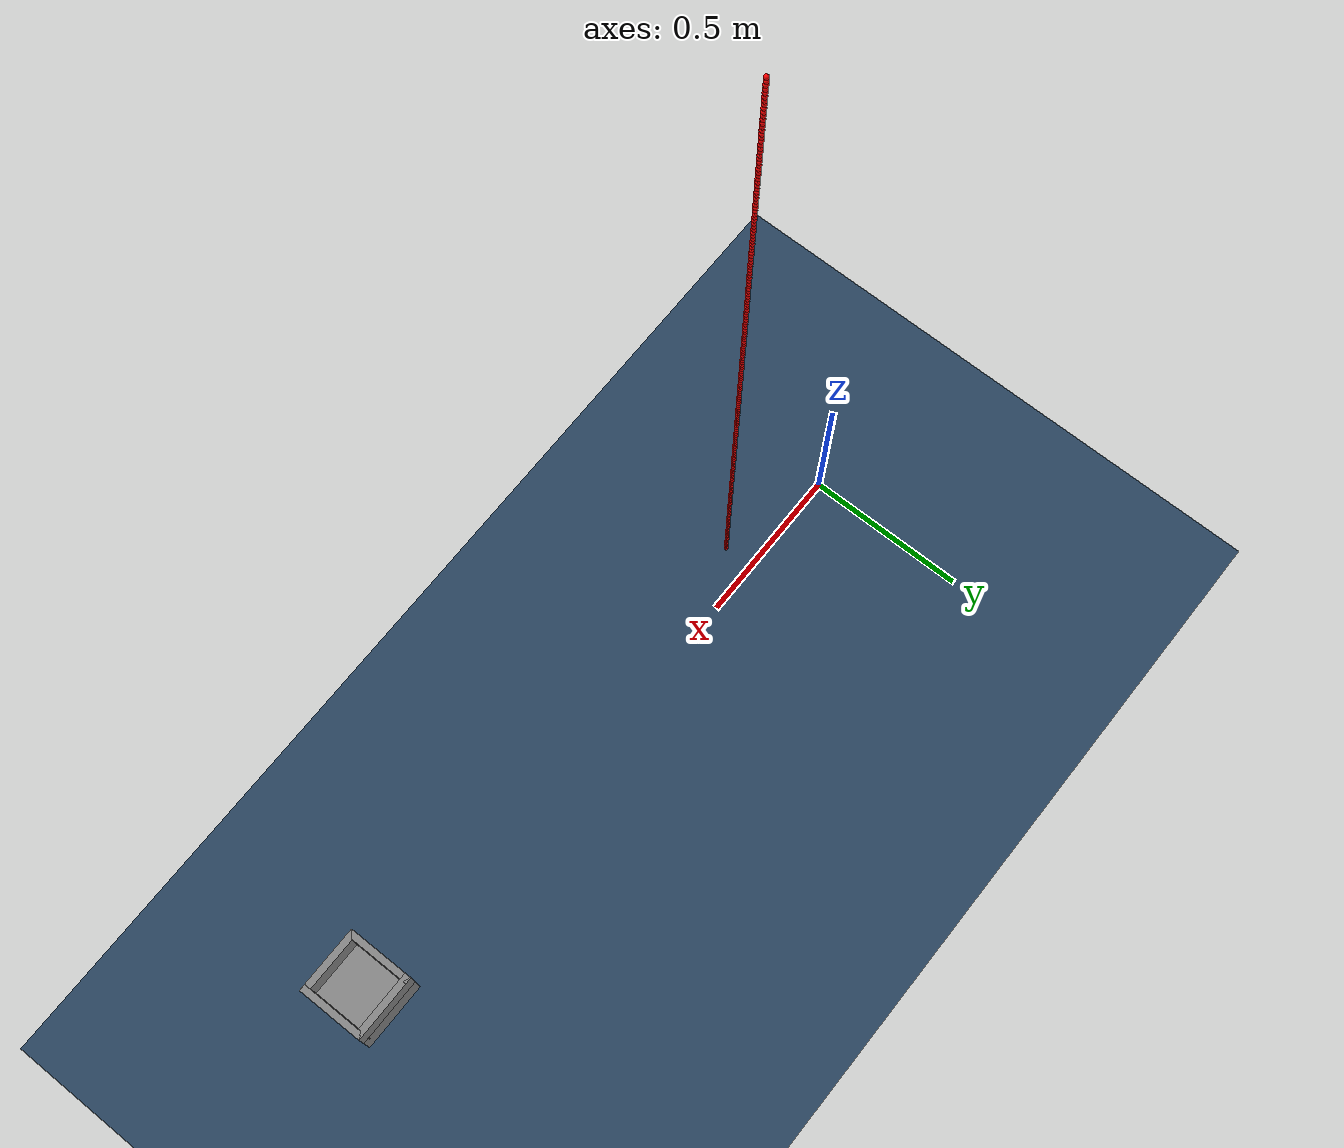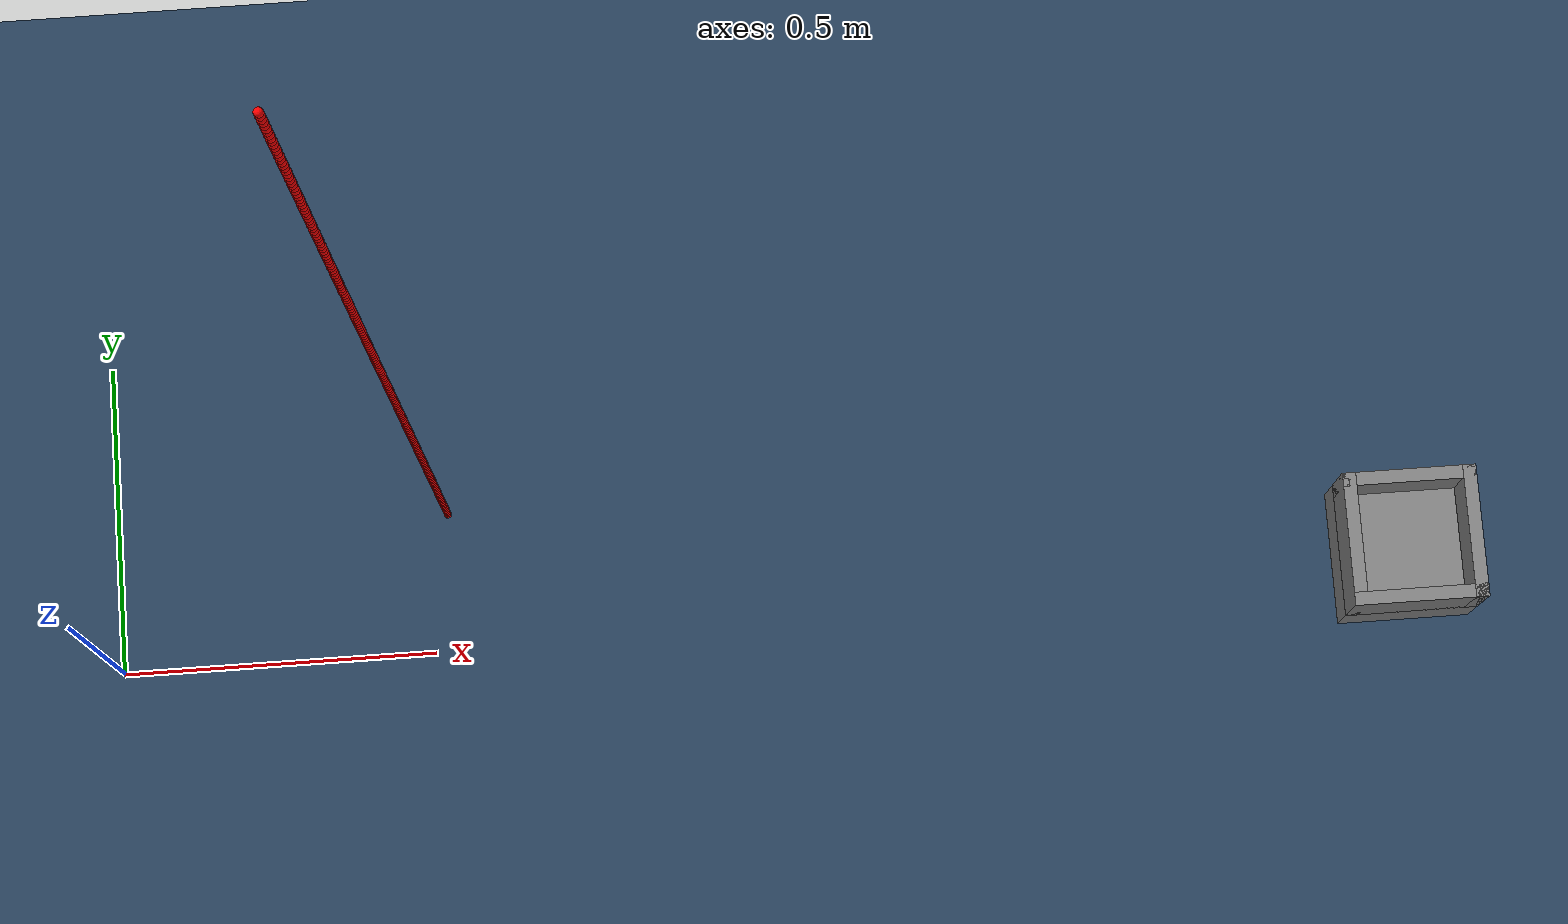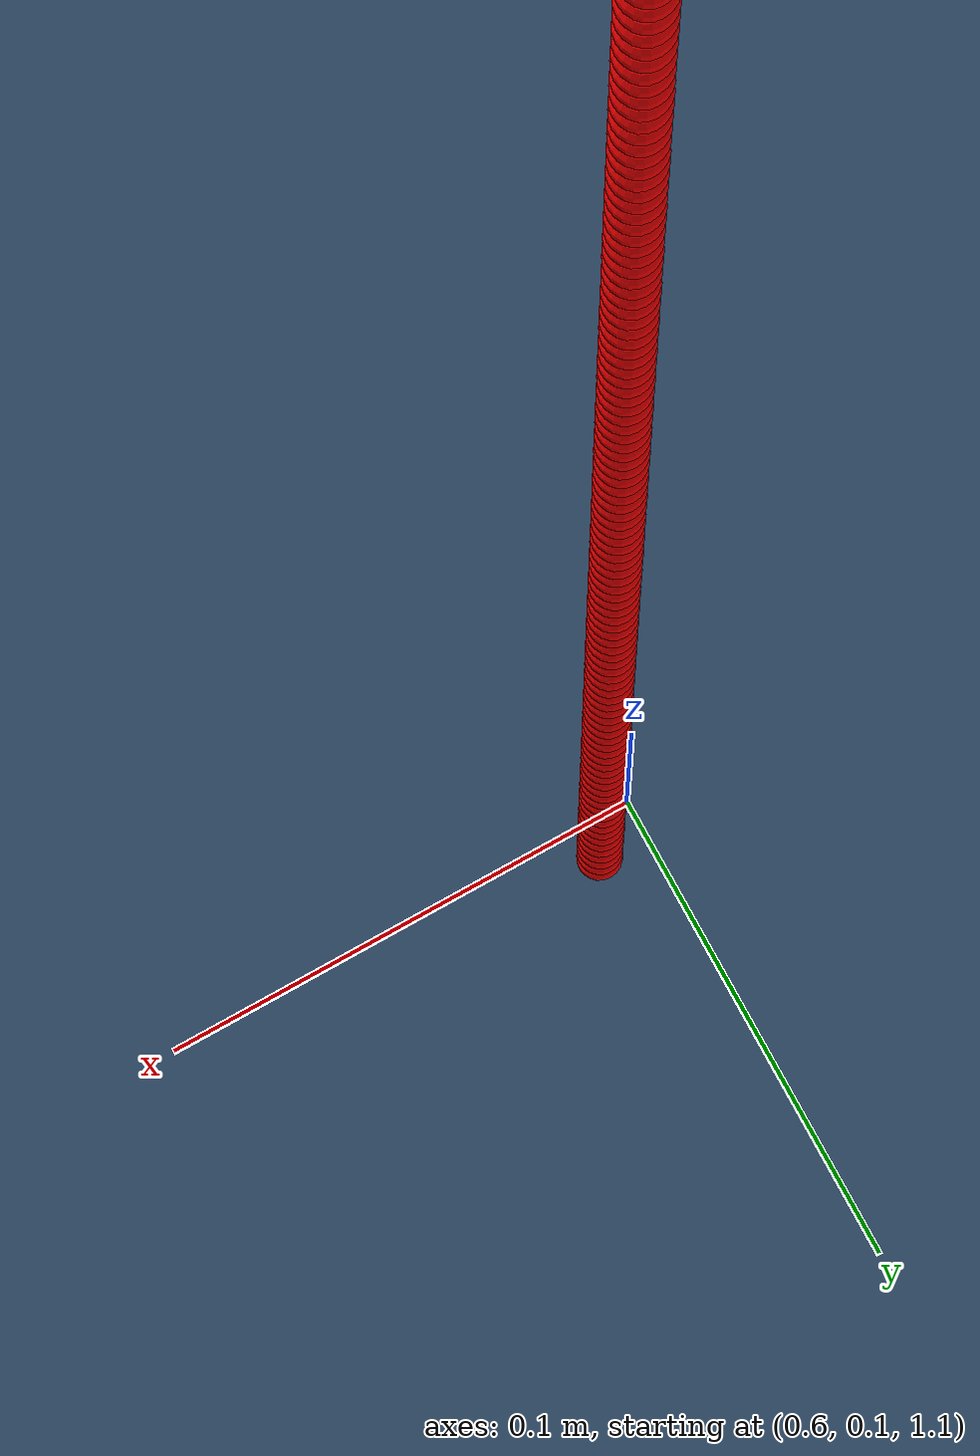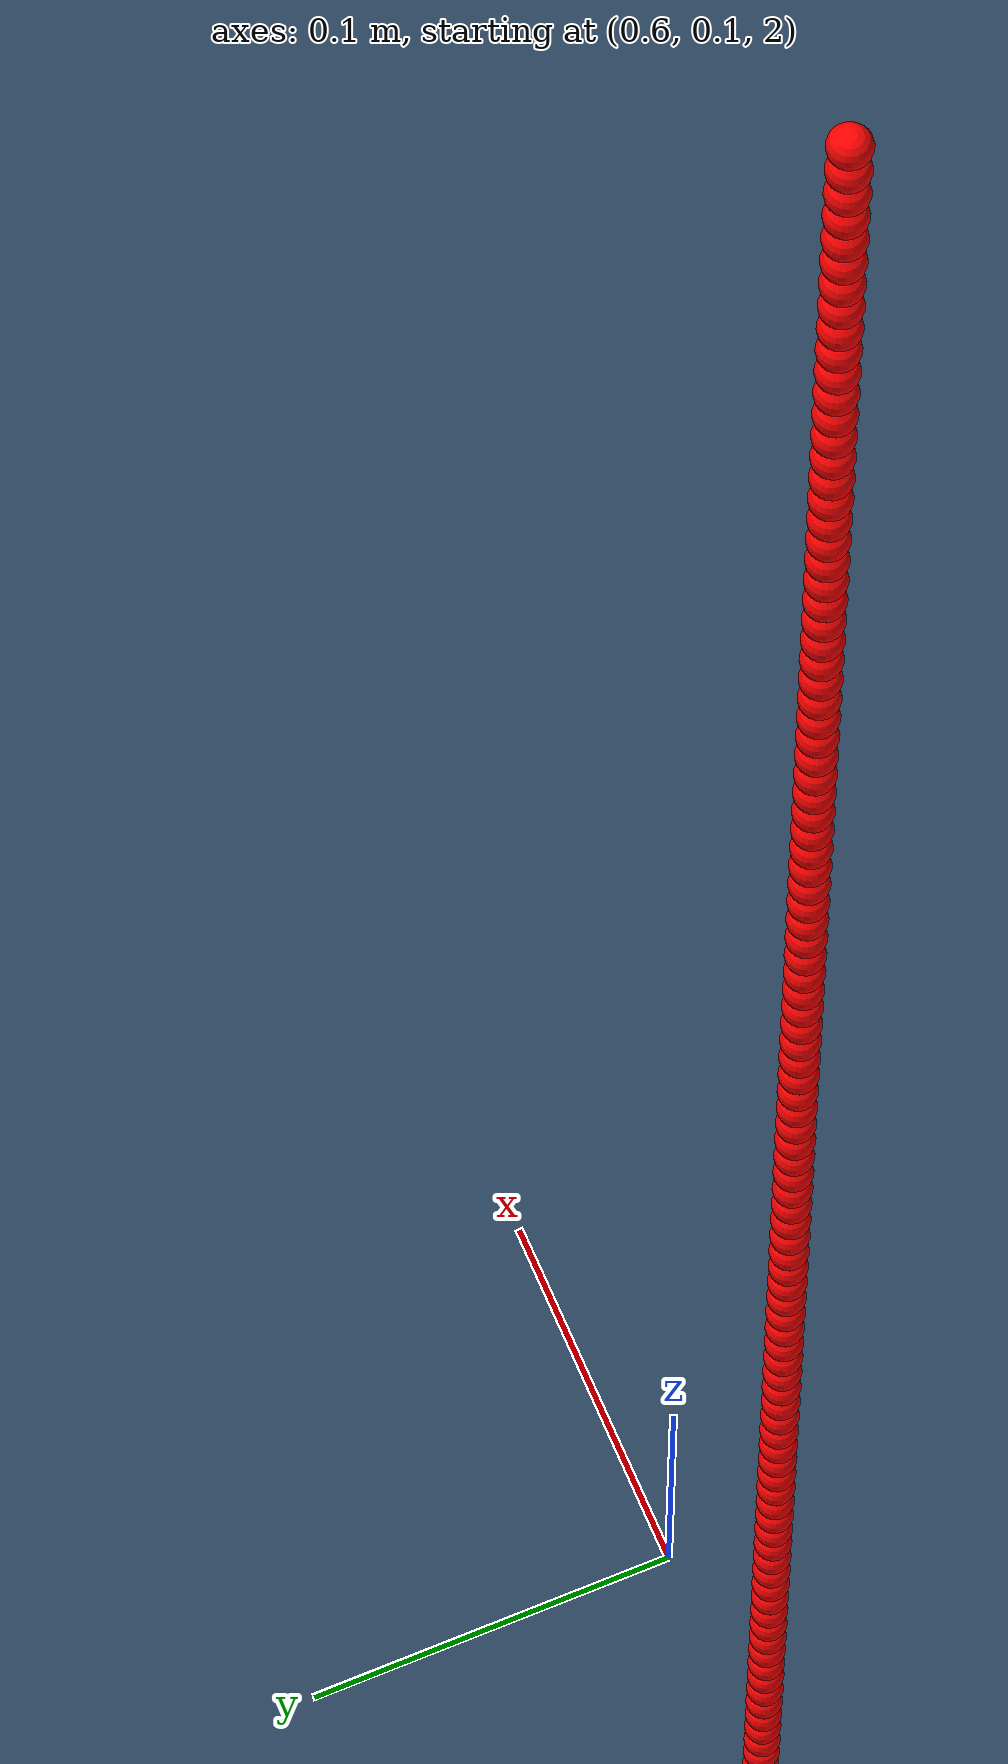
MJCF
<mujoco>
  <compiler meshdir="objects"/>
    <option timestep="0.001" integrator="RK4" solver="CG" gravity="0 0 -9.81" >
    <flag sensornoise="disable" contact="enable"/>
  </option>

<!--Activating the following deafaults increases friction of the balls, to make them appear more viscous-->

  <asset>
    <texture name="grid" type="2d" builtin="checker" width="512" height="512" rgb1=".1 .2 .3" rgb2=".2 .3 .4" />
    <material name="grid" texture="grid" texrepeat="1 1" texuniform="true" reflectance=".2" />
		<mesh name="bowl_side" file="bowl/stl/bowl_side.stl" scale="0.1 0.1 0.1"/>
    <mesh name="bowl_bottom" file="bowl/stl/bowl_bottom.stl" scale="0.1 0.1 0.1"/>
  </asset>

  <worldbody>
    <geom name="floor" size="0 0 .05" type="plane" material="grid" condim="3" />
    <light diffuse="1 1 1" pos="0 0 4" dir="0 0 -1" />
    <light diffuse="1 1 1" pos="1 -1 4" dir="0 0 -1" />
  </worldbody>

    <worldbody>

        <body name="sync_bowl" pos="2 0 0.4" >

            <geom name="bottom" type="box" size="0.1 0.1 0.05" pos="0 0 -0.04" rgba=".5 .5 .5 1"/>

            <geom name="side1" type="box" size="0.01 0.1 0.05" pos="0.09 0 0.04" rgba=".5 .5 .5 1"/>
            <geom name="side2" type="box" size="0.01 0.1 0.05" pos="-0.09 0 0.04" rgba=".5 .5 .5 1"/>
            <geom name="side3" type="box" size="0.1 0.01 0.05" pos="0 0.09 0.04" rgba=".5 .5 .5 1"/>
            <geom name="side4" type="box" size="0.1 0.01 0.05" pos="0 -0.09 0.04" rgba=".5 .5 .5 1"/>
        </body>
    </worldbody>

	<worldbody>
		<body name="sync_ball0" pos="0.59 0.075 0.8">
			<freejoint/>
			<geom name="ball0" type="sphere" size="0.005" rgba="1 0 0 1"/>
		</body>
		<body name="sync_ball1" pos="0.59 0.075 0.81">
			<freejoint/>
			<geom name="ball1" type="sphere" size="0.005" rgba="1 0 0 1"/>
		</body>
		<body name="sync_ball2" pos="0.59 0.075 0.8200000000000001">
			<freejoint/>
			<geom name="ball2" type="sphere" size="0.005" rgba="1 0 0 1"/>
		</body>
		<body name="sync_ball3" pos="0.59 0.075 0.8300000000000001">
			<freejoint/>
			<geom name="ball3" type="sphere" size="0.005" rgba="1 0 0 1"/>
		</body>
		<body name="sync_ball4" pos="0.59 0.075 0.8400000000000001">
			<freejoint/>
			<geom name="ball4" type="sphere" size="0.005" rgba="1 0 0 1"/>
		</body>
		<body name="sync_ball5" pos="0.59 0.075 0.8500000000000001">
			<freejoint/>
			<geom name="ball5" type="sphere" size="0.005" rgba="1 0 0 1"/>
		</body>
		<body name="sync_ball6" pos="0.59 0.075 0.8600000000000001">
			<freejoint/>
			<geom name="ball6" type="sphere" size="0.005" rgba="1 0 0 1"/>
		</body>
		<body name="sync_ball7" pos="0.59 0.075 0.8700000000000001">
			<freejoint/>
			<geom name="ball7" type="sphere" size="0.005" rgba="1 0 0 1"/>
		</body>
		<body name="sync_ball8" pos="0.59 0.075 0.88">
			<freejoint/>
			<geom name="ball8" type="sphere" size="0.005" rgba="1 0 0 1"/>
		</body>
		<body name="sync_ball9" pos="0.59 0.075 0.89">
			<freejoint/>
			<geom name="ball9" type="sphere" size="0.005" rgba="1 0 0 1"/>
		</body>
		<body name="sync_ball10" pos="0.59 0.075 0.9">
			<freejoint/>
			<geom name="ball10" type="sphere" size="0.005" rgba="1 0 0 1"/>
		</body>
		<body name="sync_ball11" pos="0.59 0.075 0.91">
			<freejoint/>
			<geom name="ball11" type="sphere" size="0.005" rgba="1 0 0 1"/>
		</body>
		<body name="sync_ball12" pos="0.59 0.075 0.92">
			<freejoint/>
			<geom name="ball12" type="sphere" size="0.005" rgba="1 0 0 1"/>
		</body>
		<body name="sync_ball13" pos="0.59 0.075 0.93">
			<freejoint/>
			<geom name="ball13" type="sphere" size="0.005" rgba="1 0 0 1"/>
		</body>
		<body name="sync_ball14" pos="0.59 0.075 0.9400000000000001">
			<freejoint/>
			<geom name="ball14" type="sphere" size="0.005" rgba="1 0 0 1"/>
		</body>
		<body name="sync_ball15" pos="0.59 0.075 0.9500000000000001">
			<freejoint/>
			<geom name="ball15" type="sphere" size="0.005" rgba="1 0 0 1"/>
		</body>
		<body name="sync_ball16" pos="0.59 0.075 0.9600000000000001">
			<freejoint/>
			<geom name="ball16" type="sphere" size="0.005" rgba="1 0 0 1"/>
		</body>
		<body name="sync_ball17" pos="0.59 0.075 0.9700000000000001">
			<freejoint/>
			<geom name="ball17" type="sphere" size="0.005" rgba="1 0 0 1"/>
		</body>
		<body name="sync_ball18" pos="0.59 0.075 0.98">
			<freejoint/>
			<geom name="ball18" type="sphere" size="0.005" rgba="1 0 0 1"/>
		</body>
		<body name="sync_ball19" pos="0.59 0.075 0.99">
			<freejoint/>
			<geom name="ball19" type="sphere" size="0.005" rgba="1 0 0 1"/>
		</body>
		<body name="sync_ball20" pos="0.59 0.075 1.0">
			<freejoint/>
			<geom name="ball20" type="sphere" size="0.005" rgba="1 0 0 1"/>
		</body>
		<body name="sync_ball21" pos="0.59 0.075 1.01">
			<freejoint/>
			<geom name="ball21" type="sphere" size="0.005" rgba="1 0 0 1"/>
		</body>
		<body name="sync_ball22" pos="0.59 0.075 1.02">
			<freejoint/>
			<geom name="ball22" type="sphere" size="0.005" rgba="1 0 0 1"/>
		</body>
		<body name="sync_ball23" pos="0.59 0.075 1.03">
			<freejoint/>
			<geom name="ball23" type="sphere" size="0.005" rgba="1 0 0 1"/>
		</body>
		<body name="sync_ball24" pos="0.59 0.075 1.04">
			<freejoint/>
			<geom name="ball24" type="sphere" size="0.005" rgba="1 0 0 1"/>
		</body>
		<body name="sync_ball25" pos="0.59 0.075 1.05">
			<freejoint/>
			<geom name="ball25" type="sphere" size="0.005" rgba="1 0 0 1"/>
		</body>
		<body name="sync_ball26" pos="0.59 0.075 1.06">
			<freejoint/>
			<geom name="ball26" type="sphere" size="0.005" rgba="1 0 0 1"/>
		</body>
		<body name="sync_ball27" pos="0.59 0.075 1.07">
			<freejoint/>
			<geom name="ball27" type="sphere" size="0.005" rgba="1 0 0 1"/>
		</body>
		<body name="sync_ball28" pos="0.59 0.075 1.08">
			<freejoint/>
			<geom name="ball28" type="sphere" size="0.005" rgba="1 0 0 1"/>
		</body>
		<body name="sync_ball29" pos="0.59 0.075 1.09">
			<freejoint/>
			<geom name="ball29" type="sphere" size="0.005" rgba="1 0 0 1"/>
		</body>
		<body name="sync_ball30" pos="0.59 0.075 1.1">
			<freejoint/>
			<geom name="ball30" type="sphere" size="0.005" rgba="1 0 0 1"/>
		</body>
		<body name="sync_ball31" pos="0.59 0.075 1.11">
			<freejoint/>
			<geom name="ball31" type="sphere" size="0.005" rgba="1 0 0 1"/>
		</body>
		<body name="sync_ball32" pos="0.59 0.075 1.12">
			<freejoint/>
			<geom name="ball32" type="sphere" size="0.005" rgba="1 0 0 1"/>
		</body>
		<body name="sync_ball33" pos="0.59 0.075 1.1300000000000001">
			<freejoint/>
			<geom name="ball33" type="sphere" size="0.005" rgba="1 0 0 1"/>
		</body>
		<body name="sync_ball34" pos="0.59 0.075 1.1400000000000001">
			<freejoint/>
			<geom name="ball34" type="sphere" size="0.005" rgba="1 0 0 1"/>
		</body>
		<body name="sync_ball35" pos="0.59 0.075 1.1500000000000001">
			<freejoint/>
			<geom name="ball35" type="sphere" size="0.005" rgba="1 0 0 1"/>
		</body>
		<body name="sync_ball36" pos="0.59 0.075 1.1600000000000001">
			<freejoint/>
			<geom name="ball36" type="sphere" size="0.005" rgba="1 0 0 1"/>
		</body>
		<body name="sync_ball37" pos="0.59 0.075 1.17">
			<freejoint/>
			<geom name="ball37" type="sphere" size="0.005" rgba="1 0 0 1"/>
		</body>
		<body name="sync_ball38" pos="0.59 0.075 1.1800000000000002">
			<freejoint/>
			<geom name="ball38" type="sphere" size="0.005" rgba="1 0 0 1"/>
		</body>
		<body name="sync_ball39" pos="0.59 0.075 1.19">
			<freejoint/>
			<geom name="ball39" type="sphere" size="0.005" rgba="1 0 0 1"/>
		</body>
		<body name="sync_ball40" pos="0.59 0.075 1.2000000000000002">
			<freejoint/>
			<geom name="ball40" type="sphere" size="0.005" rgba="1 0 0 1"/>
		</body>
		<body name="sync_ball41" pos="0.59 0.075 1.21">
			<freejoint/>
			<geom name="ball41" type="sphere" size="0.005" rgba="1 0 0 1"/>
		</body>
		<body name="sync_ball42" pos="0.59 0.075 1.22">
			<freejoint/>
			<geom name="ball42" type="sphere" size="0.005" rgba="1 0 0 1"/>
		</body>
		<body name="sync_ball43" pos="0.59 0.075 1.23">
			<freejoint/>
			<geom name="ball43" type="sphere" size="0.005" rgba="1 0 0 1"/>
		</body>
		<body name="sync_ball44" pos="0.59 0.075 1.24">
			<freejoint/>
			<geom name="ball44" type="sphere" size="0.005" rgba="1 0 0 1"/>
		</body>
		<body name="sync_ball45" pos="0.59 0.075 1.25">
			<freejoint/>
			<geom name="ball45" type="sphere" size="0.005" rgba="1 0 0 1"/>
		</body>
		<body name="sync_ball46" pos="0.59 0.075 1.26">
			<freejoint/>
			<geom name="ball46" type="sphere" size="0.005" rgba="1 0 0 1"/>
		</body>
		<body name="sync_ball47" pos="0.59 0.075 1.27">
			<freejoint/>
			<geom name="ball47" type="sphere" size="0.005" rgba="1 0 0 1"/>
		</body>
		<body name="sync_ball48" pos="0.59 0.075 1.28">
			<freejoint/>
			<geom name="ball48" type="sphere" size="0.005" rgba="1 0 0 1"/>
		</body>
		<body name="sync_ball49" pos="0.59 0.075 1.29">
			<freejoint/>
			<geom name="ball49" type="sphere" size="0.005" rgba="1 0 0 1"/>
		</body>
		<body name="sync_ball50" pos="0.59 0.075 1.3">
			<freejoint/>
			<geom name="ball50" type="sphere" size="0.005" rgba="1 0 0 1"/>
		</body>
		<body name="sync_ball51" pos="0.59 0.075 1.31">
			<freejoint/>
			<geom name="ball51" type="sphere" size="0.005" rgba="1 0 0 1"/>
		</body>
		<body name="sync_ball52" pos="0.59 0.075 1.32">
			<freejoint/>
			<geom name="ball52" type="sphere" size="0.005" rgba="1 0 0 1"/>
		</body>
		<body name="sync_ball53" pos="0.59 0.075 1.33">
			<freejoint/>
			<geom name="ball53" type="sphere" size="0.005" rgba="1 0 0 1"/>
		</body>
		<body name="sync_ball54" pos="0.59 0.075 1.34">
			<freejoint/>
			<geom name="ball54" type="sphere" size="0.005" rgba="1 0 0 1"/>
		</body>
		<body name="sync_ball55" pos="0.59 0.075 1.35">
			<freejoint/>
			<geom name="ball55" type="sphere" size="0.005" rgba="1 0 0 1"/>
		</body>
		<body name="sync_ball56" pos="0.59 0.075 1.36">
			<freejoint/>
			<geom name="ball56" type="sphere" size="0.005" rgba="1 0 0 1"/>
		</body>
		<body name="sync_ball57" pos="0.59 0.075 1.37">
			<freejoint/>
			<geom name="ball57" type="sphere" size="0.005" rgba="1 0 0 1"/>
		</body>
		<body name="sync_ball58" pos="0.59 0.075 1.38">
			<freejoint/>
			<geom name="ball58" type="sphere" size="0.005" rgba="1 0 0 1"/>
		</body>
		<body name="sync_ball59" pos="0.59 0.075 1.3900000000000001">
			<freejoint/>
			<geom name="ball59" type="sphere" size="0.005" rgba="1 0 0 1"/>
		</body>
		<body name="sync_ball60" pos="0.59 0.075 1.4">
			<freejoint/>
			<geom name="ball60" type="sphere" size="0.005" rgba="1 0 0 1"/>
		</body>
		<body name="sync_ball61" pos="0.59 0.075 1.4100000000000001">
			<freejoint/>
			<geom name="ball61" type="sphere" size="0.005" rgba="1 0 0 1"/>
		</body>
		<body name="sync_ball62" pos="0.59 0.075 1.42">
			<freejoint/>
			<geom name="ball62" type="sphere" size="0.005" rgba="1 0 0 1"/>
		</body>
		<body name="sync_ball63" pos="0.59 0.075 1.4300000000000002">
			<freejoint/>
			<geom name="ball63" type="sphere" size="0.005" rgba="1 0 0 1"/>
		</body>
		<body name="sync_ball64" pos="0.59 0.075 1.44">
			<freejoint/>
			<geom name="ball64" type="sphere" size="0.005" rgba="1 0 0 1"/>
		</body>
		<body name="sync_ball65" pos="0.59 0.075 1.4500000000000002">
			<freejoint/>
			<geom name="ball65" type="sphere" size="0.005" rgba="1 0 0 1"/>
		</body>
		<body name="sync_ball66" pos="0.59 0.075 1.46">
			<freejoint/>
			<geom name="ball66" type="sphere" size="0.005" rgba="1 0 0 1"/>
		</body>
		<body name="sync_ball67" pos="0.59 0.075 1.4700000000000002">
			<freejoint/>
			<geom name="ball67" type="sphere" size="0.005" rgba="1 0 0 1"/>
		</body>
		<body name="sync_ball68" pos="0.59 0.075 1.48">
			<freejoint/>
			<geom name="ball68" type="sphere" size="0.005" rgba="1 0 0 1"/>
		</body>
		<body name="sync_ball69" pos="0.59 0.075 1.4900000000000002">
			<freejoint/>
			<geom name="ball69" type="sphere" size="0.005" rgba="1 0 0 1"/>
		</body>
		<body name="sync_ball70" pos="0.59 0.075 1.5">
			<freejoint/>
			<geom name="ball70" type="sphere" size="0.005" rgba="1 0 0 1"/>
		</body>
		<body name="sync_ball71" pos="0.59 0.075 1.51">
			<freejoint/>
			<geom name="ball71" type="sphere" size="0.005" rgba="1 0 0 1"/>
		</body>
		<body name="sync_ball72" pos="0.59 0.075 1.52">
			<freejoint/>
			<geom name="ball72" type="sphere" size="0.005" rgba="1 0 0 1"/>
		</body>
		<body name="sync_ball73" pos="0.59 0.075 1.53">
			<freejoint/>
			<geom name="ball73" type="sphere" size="0.005" rgba="1 0 0 1"/>
		</body>
		<body name="sync_ball74" pos="0.59 0.075 1.54">
			<freejoint/>
			<geom name="ball74" type="sphere" size="0.005" rgba="1 0 0 1"/>
		</body>
		<body name="sync_ball75" pos="0.59 0.075 1.55">
			<freejoint/>
			<geom name="ball75" type="sphere" size="0.005" rgba="1 0 0 1"/>
		</body>
		<body name="sync_ball76" pos="0.59 0.075 1.56">
			<freejoint/>
			<geom name="ball76" type="sphere" size="0.005" rgba="1 0 0 1"/>
		</body>
		<body name="sync_ball77" pos="0.59 0.075 1.57">
			<freejoint/>
			<geom name="ball77" type="sphere" size="0.005" rgba="1 0 0 1"/>
		</body>
		<body name="sync_ball78" pos="0.59 0.075 1.58">
			<freejoint/>
			<geom name="ball78" type="sphere" size="0.005" rgba="1 0 0 1"/>
		</body>
		<body name="sync_ball79" pos="0.59 0.075 1.59">
			<freejoint/>
			<geom name="ball79" type="sphere" size="0.005" rgba="1 0 0 1"/>
		</body>
		<body name="sync_ball80" pos="0.59 0.075 1.6">
			<freejoint/>
			<geom name="ball80" type="sphere" size="0.005" rgba="1 0 0 1"/>
		</body>
		<body name="sync_ball81" pos="0.59 0.075 1.61">
			<freejoint/>
			<geom name="ball81" type="sphere" size="0.005" rgba="1 0 0 1"/>
		</body>
		<body name="sync_ball82" pos="0.59 0.075 1.62">
			<freejoint/>
			<geom name="ball82" type="sphere" size="0.005" rgba="1 0 0 1"/>
		</body>
		<body name="sync_ball83" pos="0.59 0.075 1.6300000000000001">
			<freejoint/>
			<geom name="ball83" type="sphere" size="0.005" rgba="1 0 0 1"/>
		</body>
		<body name="sync_ball84" pos="0.59 0.075 1.6400000000000001">
			<freejoint/>
			<geom name="ball84" type="sphere" size="0.005" rgba="1 0 0 1"/>
		</body>
		<body name="sync_ball85" pos="0.59 0.075 1.65">
			<freejoint/>
			<geom name="ball85" type="sphere" size="0.005" rgba="1 0 0 1"/>
		</body>
		<body name="sync_ball86" pos="0.59 0.075 1.6600000000000001">
			<freejoint/>
			<geom name="ball86" type="sphere" size="0.005" rgba="1 0 0 1"/>
		</body>
		<body name="sync_ball87" pos="0.59 0.075 1.67">
			<freejoint/>
			<geom name="ball87" type="sphere" size="0.005" rgba="1 0 0 1"/>
		</body>
		<body name="sync_ball88" pos="0.59 0.075 1.6800000000000002">
			<freejoint/>
			<geom name="ball88" type="sphere" size="0.005" rgba="1 0 0 1"/>
		</body>
		<body name="sync_ball89" pos="0.59 0.075 1.69">
			<freejoint/>
			<geom name="ball89" type="sphere" size="0.005" rgba="1 0 0 1"/>
		</body>
		<body name="sync_ball90" pos="0.59 0.075 1.7000000000000002">
			<freejoint/>
			<geom name="ball90" type="sphere" size="0.005" rgba="1 0 0 1"/>
		</body>
		<body name="sync_ball91" pos="0.59 0.075 1.71">
			<freejoint/>
			<geom name="ball91" type="sphere" size="0.005" rgba="1 0 0 1"/>
		</body>
		<body name="sync_ball92" pos="0.59 0.075 1.7200000000000002">
			<freejoint/>
			<geom name="ball92" type="sphere" size="0.005" rgba="1 0 0 1"/>
		</body>
		<body name="sync_ball93" pos="0.59 0.075 1.73">
			<freejoint/>
			<geom name="ball93" type="sphere" size="0.005" rgba="1 0 0 1"/>
		</body>
		<body name="sync_ball94" pos="0.59 0.075 1.7400000000000002">
			<freejoint/>
			<geom name="ball94" type="sphere" size="0.005" rgba="1 0 0 1"/>
		</body>
		<body name="sync_ball95" pos="0.59 0.075 1.75">
			<freejoint/>
			<geom name="ball95" type="sphere" size="0.005" rgba="1 0 0 1"/>
		</body>
		<body name="sync_ball96" pos="0.59 0.075 1.76">
			<freejoint/>
			<geom name="ball96" type="sphere" size="0.005" rgba="1 0 0 1"/>
		</body>
		<body name="sync_ball97" pos="0.59 0.075 1.77">
			<freejoint/>
			<geom name="ball97" type="sphere" size="0.005" rgba="1 0 0 1"/>
		</body>
		<body name="sync_ball98" pos="0.59 0.075 1.78">
			<freejoint/>
			<geom name="ball98" type="sphere" size="0.005" rgba="1 0 0 1"/>
		</body>
		<body name="sync_ball99" pos="0.59 0.075 1.79">
			<freejoint/>
			<geom name="ball99" type="sphere" size="0.005" rgba="1 0 0 1"/>
		</body>
		<body name="sync_ball100" pos="0.59 0.075 1.8">
			<freejoint/>
			<geom name="ball100" type="sphere" size="0.005" rgba="1 0 0 1"/>
		</body>
		<body name="sync_ball101" pos="0.59 0.075 1.81">
			<freejoint/>
			<geom name="ball101" type="sphere" size="0.005" rgba="1 0 0 1"/>
		</body>
		<body name="sync_ball102" pos="0.59 0.075 1.82">
			<freejoint/>
			<geom name="ball102" type="sphere" size="0.005" rgba="1 0 0 1"/>
		</body>
		<body name="sync_ball103" pos="0.59 0.075 1.83">
			<freejoint/>
			<geom name="ball103" type="sphere" size="0.005" rgba="1 0 0 1"/>
		</body>
		<body name="sync_ball104" pos="0.59 0.075 1.84">
			<freejoint/>
			<geom name="ball104" type="sphere" size="0.005" rgba="1 0 0 1"/>
		</body>
		<body name="sync_ball105" pos="0.59 0.075 1.85">
			<freejoint/>
			<geom name="ball105" type="sphere" size="0.005" rgba="1 0 0 1"/>
		</body>
		<body name="sync_ball106" pos="0.59 0.075 1.86">
			<freejoint/>
			<geom name="ball106" type="sphere" size="0.005" rgba="1 0 0 1"/>
		</body>
		<body name="sync_ball107" pos="0.59 0.075 1.87">
			<freejoint/>
			<geom name="ball107" type="sphere" size="0.005" rgba="1 0 0 1"/>
		</body>
		<body name="sync_ball108" pos="0.59 0.075 1.8800000000000001">
			<freejoint/>
			<geom name="ball108" type="sphere" size="0.005" rgba="1 0 0 1"/>
		</body>
		<body name="sync_ball109" pos="0.59 0.075 1.8900000000000001">
			<freejoint/>
			<geom name="ball109" type="sphere" size="0.005" rgba="1 0 0 1"/>
		</body>
		<body name="sync_ball110" pos="0.59 0.075 1.9000000000000001">
			<freejoint/>
			<geom name="ball110" type="sphere" size="0.005" rgba="1 0 0 1"/>
		</body>
		<body name="sync_ball111" pos="0.59 0.075 1.9100000000000001">
			<freejoint/>
			<geom name="ball111" type="sphere" size="0.005" rgba="1 0 0 1"/>
		</body>
		<body name="sync_ball112" pos="0.59 0.075 1.9200000000000002">
			<freejoint/>
			<geom name="ball112" type="sphere" size="0.005" rgba="1 0 0 1"/>
		</body>
		<body name="sync_ball113" pos="0.59 0.075 1.9300000000000002">
			<freejoint/>
			<geom name="ball113" type="sphere" size="0.005" rgba="1 0 0 1"/>
		</body>
		<body name="sync_ball114" pos="0.59 0.075 1.9400000000000002">
			<freejoint/>
			<geom name="ball114" type="sphere" size="0.005" rgba="1 0 0 1"/>
		</body>
		<body name="sync_ball115" pos="0.59 0.075 1.9500000000000002">
			<freejoint/>
			<geom name="ball115" type="sphere" size="0.005" rgba="1 0 0 1"/>
		</body>
		<body name="sync_ball116" pos="0.59 0.075 1.96">
			<freejoint/>
			<geom name="ball116" type="sphere" size="0.005" rgba="1 0 0 1"/>
		</body>
		<body name="sync_ball117" pos="0.59 0.075 1.97">
			<freejoint/>
			<geom name="ball117" type="sphere" size="0.005" rgba="1 0 0 1"/>
		</body>
		<body name="sync_ball118" pos="0.59 0.075 1.98">
			<freejoint/>
			<geom name="ball118" type="sphere" size="0.005" rgba="1 0 0 1"/>
		</body>
		<body name="sync_ball119" pos="0.59 0.075 1.99">
			<freejoint/>
			<geom name="ball119" type="sphere" size="0.005" rgba="1 0 0 1"/>
		</body>
		<body name="sync_ball120" pos="0.59 0.075 2.0">
			<freejoint/>
			<geom name="ball120" type="sphere" size="0.005" rgba="1 0 0 1"/>
		</body>
		<body name="sync_ball121" pos="0.59 0.075 2.01">
			<freejoint/>
			<geom name="ball121" type="sphere" size="0.005" rgba="1 0 0 1"/>
		</body>
		<body name="sync_ball122" pos="0.59 0.075 2.02">
			<freejoint/>
			<geom name="ball122" type="sphere" size="0.005" rgba="1 0 0 1"/>
		</body>
		<body name="sync_ball123" pos="0.59 0.075 2.0300000000000002">
			<freejoint/>
			<geom name="ball123" type="sphere" size="0.005" rgba="1 0 0 1"/>
		</body>
		<body name="sync_ball124" pos="0.59 0.075 2.04">
			<freejoint/>
			<geom name="ball124" type="sphere" size="0.005" rgba="1 0 0 1"/>
		</body>
		<body name="sync_ball125" pos="0.59 0.075 2.05">
			<freejoint/>
			<geom name="ball125" type="sphere" size="0.005" rgba="1 0 0 1"/>
		</body>
		<body name="sync_ball126" pos="0.59 0.075 2.06">
			<freejoint/>
			<geom name="ball126" type="sphere" size="0.005" rgba="1 0 0 1"/>
		</body>
		<body name="sync_ball127" pos="0.59 0.075 2.0700000000000003">
			<freejoint/>
			<geom name="ball127" type="sphere" size="0.005" rgba="1 0 0 1"/>
		</body>
		<body name="sync_ball128" pos="0.59 0.075 2.08">
			<freejoint/>
			<geom name="ball128" type="sphere" size="0.005" rgba="1 0 0 1"/>
		</body>
		<body name="sync_ball129" pos="0.59 0.075 2.09">
			<freejoint/>
			<geom name="ball129" type="sphere" size="0.005" rgba="1 0 0 1"/>
		</body>
		<body name="sync_ball130" pos="0.59 0.075 2.1">
			<freejoint/>
			<geom name="ball130" type="sphere" size="0.005" rgba="1 0 0 1"/>
		</body>
		<body name="sync_ball131" pos="0.59 0.075 2.1100000000000003">
			<freejoint/>
			<geom name="ball131" type="sphere" size="0.005" rgba="1 0 0 1"/>
		</body>
		<body name="sync_ball132" pos="0.59 0.075 2.12">
			<freejoint/>
			<geom name="ball132" type="sphere" size="0.005" rgba="1 0 0 1"/>
		</body>
		<body name="sync_ball133" pos="0.59 0.075 2.13">
			<freejoint/>
			<geom name="ball133" type="sphere" size="0.005" rgba="1 0 0 1"/>
		</body>
		<body name="sync_ball134" pos="0.59 0.075 2.14">
			<freejoint/>
			<geom name="ball134" type="sphere" size="0.005" rgba="1 0 0 1"/>
		</body>
		<body name="sync_ball135" pos="0.59 0.075 2.1500000000000004">
			<freejoint/>
			<geom name="ball135" type="sphere" size="0.005" rgba="1 0 0 1"/>
		</body>
		<body name="sync_ball136" pos="0.59 0.075 2.16">
			<freejoint/>
			<geom name="ball136" type="sphere" size="0.005" rgba="1 0 0 1"/>
		</body>
		<body name="sync_ball137" pos="0.59 0.075 2.17">
			<freejoint/>
			<geom name="ball137" type="sphere" size="0.005" rgba="1 0 0 1"/>
		</body>
		<body name="sync_ball138" pos="0.59 0.075 2.18">
			<freejoint/>
			<geom name="ball138" type="sphere" size="0.005" rgba="1 0 0 1"/>
		</body>
		<body name="sync_ball139" pos="0.59 0.075 2.1900000000000004">
			<freejoint/>
			<geom name="ball139" type="sphere" size="0.005" rgba="1 0 0 1"/>
		</body>
		<body name="sync_ball140" pos="0.59 0.075 2.2">
			<freejoint/>
			<geom name="ball140" type="sphere" size="0.005" rgba="1 0 0 1"/>
		</body>
		<body name="sync_ball141" pos="0.59 0.075 2.21">
			<freejoint/>
			<geom name="ball141" type="sphere" size="0.005" rgba="1 0 0 1"/>
		</body>
		<body name="sync_ball142" pos="0.59 0.075 2.2199999999999998">
			<freejoint/>
			<geom name="ball142" type="sphere" size="0.005" rgba="1 0 0 1"/>
		</body>
		<body name="sync_ball143" pos="0.59 0.075 2.23">
			<freejoint/>
			<geom name="ball143" type="sphere" size="0.005" rgba="1 0 0 1"/>
		</body>
		<body name="sync_ball144" pos="0.59 0.075 2.24">
			<freejoint/>
			<geom name="ball144" type="sphere" size="0.005" rgba="1 0 0 1"/>
		</body>
		<body name="sync_ball145" pos="0.59 0.075 2.25">
			<freejoint/>
			<geom name="ball145" type="sphere" size="0.005" rgba="1 0 0 1"/>
		</body>
		<body name="sync_ball146" pos="0.59 0.075 2.26">
			<freejoint/>
			<geom name="ball146" type="sphere" size="0.005" rgba="1 0 0 1"/>
		</body>
		<body name="sync_ball147" pos="0.59 0.075 2.27">
			<freejoint/>
			<geom name="ball147" type="sphere" size="0.005" rgba="1 0 0 1"/>
		</body>
		<body name="sync_ball148" pos="0.59 0.075 2.2800000000000002">
			<freejoint/>
			<geom name="ball148" type="sphere" size="0.005" rgba="1 0 0 1"/>
		</body>
		<body name="sync_ball149" pos="0.59 0.075 2.29">
			<freejoint/>
			<geom name="ball149" type="sphere" size="0.005" rgba="1 0 0 1"/>
		</body>
		<body name="sync_ball150" pos="0.59 0.075 2.3">
			<freejoint/>
			<geom name="ball150" type="sphere" size="0.005" rgba="1 0 0 1"/>
		</body>
		<body name="sync_ball151" pos="0.59 0.075 2.31">
			<freejoint/>
			<geom name="ball151" type="sphere" size="0.005" rgba="1 0 0 1"/>
		</body>
		<body name="sync_ball152" pos="0.59 0.075 2.3200000000000003">
			<freejoint/>
			<geom name="ball152" type="sphere" size="0.005" rgba="1 0 0 1"/>
		</body>
		<body name="sync_ball153" pos="0.59 0.075 2.33">
			<freejoint/>
			<geom name="ball153" type="sphere" size="0.005" rgba="1 0 0 1"/>
		</body>
		<body name="sync_ball154" pos="0.59 0.075 2.34">
			<freejoint/>
			<geom name="ball154" type="sphere" size="0.005" rgba="1 0 0 1"/>
		</body>
		<body name="sync_ball155" pos="0.59 0.075 2.35">
			<freejoint/>
			<geom name="ball155" type="sphere" size="0.005" rgba="1 0 0 1"/>
		</body>
		<body name="sync_ball156" pos="0.59 0.075 2.3600000000000003">
			<freejoint/>
			<geom name="ball156" type="sphere" size="0.005" rgba="1 0 0 1"/>
		</body>
		<body name="sync_ball157" pos="0.59 0.075 2.37">
			<freejoint/>
			<geom name="ball157" type="sphere" size="0.005" rgba="1 0 0 1"/>
		</body>
		<body name="sync_ball158" pos="0.59 0.075 2.38">
			<freejoint/>
			<geom name="ball158" type="sphere" size="0.005" rgba="1 0 0 1"/>
		</body>
		<body name="sync_ball159" pos="0.59 0.075 2.39">
			<freejoint/>
			<geom name="ball159" type="sphere" size="0.005" rgba="1 0 0 1"/>
		</body>
		<body name="sync_ball160" pos="0.59 0.075 2.4000000000000004">
			<freejoint/>
			<geom name="ball160" type="sphere" size="0.005" rgba="1 0 0 1"/>
		</body>
		<body name="sync_ball161" pos="0.59 0.075 2.41">
			<freejoint/>
			<geom name="ball161" type="sphere" size="0.005" rgba="1 0 0 1"/>
		</body>
		<body name="sync_ball162" pos="0.59 0.075 2.42">
			<freejoint/>
			<geom name="ball162" type="sphere" size="0.005" rgba="1 0 0 1"/>
		</body>
		<body name="sync_ball163" pos="0.59 0.075 2.43">
			<freejoint/>
			<geom name="ball163" type="sphere" size="0.005" rgba="1 0 0 1"/>
		</body>
		<body name="sync_ball164" pos="0.59 0.075 2.4400000000000004">
			<freejoint/>
			<geom name="ball164" type="sphere" size="0.005" rgba="1 0 0 1"/>
		</body>
		<body name="sync_ball165" pos="0.59 0.075 2.45">
			<freejoint/>
			<geom name="ball165" type="sphere" size="0.005" rgba="1 0 0 1"/>
		</body>
		<body name="sync_ball166" pos="0.59 0.075 2.46">
			<freejoint/>
			<geom name="ball166" type="sphere" size="0.005" rgba="1 0 0 1"/>
		</body>
		<body name="sync_ball167" pos="0.59 0.075 2.4699999999999998">
			<freejoint/>
			<geom name="ball167" type="sphere" size="0.005" rgba="1 0 0 1"/>
		</body>
		<body name="sync_ball168" pos="0.59 0.075 2.48">
			<freejoint/>
			<geom name="ball168" type="sphere" size="0.005" rgba="1 0 0 1"/>
		</body>
		<body name="sync_ball169" pos="0.59 0.075 2.49">
			<freejoint/>
			<geom name="ball169" type="sphere" size="0.005" rgba="1 0 0 1"/>
		</body>
		<body name="sync_ball170" pos="0.59 0.075 2.5">
			<freejoint/>
			<geom name="ball170" type="sphere" size="0.005" rgba="1 0 0 1"/>
		</body>
		<body name="sync_ball171" pos="0.59 0.075 2.51">
			<freejoint/>
			<geom name="ball171" type="sphere" size="0.005" rgba="1 0 0 1"/>
		</body>
		<body name="sync_ball172" pos="0.59 0.075 2.52">
			<freejoint/>
			<geom name="ball172" type="sphere" size="0.005" rgba="1 0 0 1"/>
		</body>
		<body name="sync_ball173" pos="0.59 0.075 2.5300000000000002">
			<freejoint/>
			<geom name="ball173" type="sphere" size="0.005" rgba="1 0 0 1"/>
		</body>
		<body name="sync_ball174" pos="0.59 0.075 2.54">
			<freejoint/>
			<geom name="ball174" type="sphere" size="0.005" rgba="1 0 0 1"/>
		</body>
		<body name="sync_ball175" pos="0.59 0.075 2.55">
			<freejoint/>
			<geom name="ball175" type="sphere" size="0.005" rgba="1 0 0 1"/>
		</body>
		<body name="sync_ball176" pos="0.59 0.075 2.56">
			<freejoint/>
			<geom name="ball176" type="sphere" size="0.005" rgba="1 0 0 1"/>
		</body>
		<body name="sync_ball177" pos="0.59 0.075 2.5700000000000003">
			<freejoint/>
			<geom name="ball177" type="sphere" size="0.005" rgba="1 0 0 1"/>
		</body>
		<body name="sync_ball178" pos="0.59 0.075 2.58">
			<freejoint/>
			<geom name="ball178" type="sphere" size="0.005" rgba="1 0 0 1"/>
		</body>
		<body name="sync_ball179" pos="0.59 0.075 2.59">
			<freejoint/>
			<geom name="ball179" type="sphere" size="0.005" rgba="1 0 0 1"/>
		</body>
		<body name="sync_ball180" pos="0.59 0.075 2.6">
			<freejoint/>
			<geom name="ball180" type="sphere" size="0.005" rgba="1 0 0 1"/>
		</body>
		<body name="sync_ball181" pos="0.59 0.075 2.6100000000000003">
			<freejoint/>
			<geom name="ball181" type="sphere" size="0.005" rgba="1 0 0 1"/>
		</body>
		<body name="sync_ball182" pos="0.59 0.075 2.62">
			<freejoint/>
			<geom name="ball182" type="sphere" size="0.005" rgba="1 0 0 1"/>
		</body>
		<body name="sync_ball183" pos="0.59 0.075 2.63">
			<freejoint/>
			<geom name="ball183" type="sphere" size="0.005" rgba="1 0 0 1"/>
		</body>
		<body name="sync_ball184" pos="0.59 0.075 2.64">
			<freejoint/>
			<geom name="ball184" type="sphere" size="0.005" rgba="1 0 0 1"/>
		</body>
		<body name="sync_ball185" pos="0.59 0.075 2.6500000000000004">
			<freejoint/>
			<geom name="ball185" type="sphere" size="0.005" rgba="1 0 0 1"/>
		</body>
		<body name="sync_ball186" pos="0.59 0.075 2.66">
			<freejoint/>
			<geom name="ball186" type="sphere" size="0.005" rgba="1 0 0 1"/>
		</body>
		<body name="sync_ball187" pos="0.59 0.075 2.67">
			<freejoint/>
			<geom name="ball187" type="sphere" size="0.005" rgba="1 0 0 1"/>
		</body>
		<body name="sync_ball188" pos="0.59 0.075 2.68">
			<freejoint/>
			<geom name="ball188" type="sphere" size="0.005" rgba="1 0 0 1"/>
		</body>
		<body name="sync_ball189" pos="0.59 0.075 2.6900000000000004">
			<freejoint/>
			<geom name="ball189" type="sphere" size="0.005" rgba="1 0 0 1"/>
		</body>
		<body name="sync_ball190" pos="0.59 0.075 2.7">
			<freejoint/>
			<geom name="ball190" type="sphere" size="0.005" rgba="1 0 0 1"/>
		</body>
		<body name="sync_ball191" pos="0.59 0.075 2.71">
			<freejoint/>
			<geom name="ball191" type="sphere" size="0.005" rgba="1 0 0 1"/>
		</body>
		<body name="sync_ball192" pos="0.59 0.075 2.7199999999999998">
			<freejoint/>
			<geom name="ball192" type="sphere" size="0.005" rgba="1 0 0 1"/>
		</body>
		<body name="sync_ball193" pos="0.59 0.075 2.73">
			<freejoint/>
			<geom name="ball193" type="sphere" size="0.005" rgba="1 0 0 1"/>
		</body>
		<body name="sync_ball194" pos="0.59 0.075 2.74">
			<freejoint/>
			<geom name="ball194" type="sphere" size="0.005" rgba="1 0 0 1"/>
		</body>
		<body name="sync_ball195" pos="0.59 0.075 2.75">
			<freejoint/>
			<geom name="ball195" type="sphere" size="0.005" rgba="1 0 0 1"/>
		</body>
		<body name="sync_ball196" pos="0.59 0.075 2.76">
			<freejoint/>
			<geom name="ball196" type="sphere" size="0.005" rgba="1 0 0 1"/>
		</body>
		<body name="sync_ball197" pos="0.59 0.075 2.77">
			<freejoint/>
			<geom name="ball197" type="sphere" size="0.005" rgba="1 0 0 1"/>
		</body>
		<body name="sync_ball198" pos="0.59 0.075 2.7800000000000002">
			<freejoint/>
			<geom name="ball198" type="sphere" size="0.005" rgba="1 0 0 1"/>
		</body>
		<body name="sync_ball199" pos="0.59 0.075 2.79">
			<freejoint/>
			<geom name="ball199" type="sphere" size="0.005" rgba="1 0 0 1"/>
		</body>
	</worldbody>

<!--Activating the following contact pairs makes the balls bounce from the bottom of the container-->
<contact>
 <pair geom1="ball0" geom2="bottom" solref="0.01 0.4"/>
</contact>
<contact>
 <pair geom1="ball1" geom2="bottom" solref="0.01 0.4"/>
</contact>
<contact>
 <pair geom1="ball2" geom2="bottom" solref="0.01 0.4"/>
</contact>
<contact>
 <pair geom1="ball3" geom2="bottom" solref="0.01 0.4"/>
</contact>
<contact>
 <pair geom1="ball4" geom2="bottom" solref="0.01 0.4"/>
</contact>
<contact>
 <pair geom1="ball5" geom2="bottom" solref="0.01 0.4"/>
</contact>
<contact>
 <pair geom1="ball6" geom2="bottom" solref="0.01 0.4"/>
</contact>
<contact>
 <pair geom1="ball7" geom2="bottom" solref="0.01 0.4"/>
</contact>
<contact>
 <pair geom1="ball8" geom2="bottom" solref="0.01 0.4"/>
</contact>
<contact>
 <pair geom1="ball9" geom2="bottom" solref="0.01 0.4"/>
</contact>
<contact>
 <pair geom1="ball10" geom2="bottom" solref="0.01 0.4"/>
</contact>
<contact>
 <pair geom1="ball11" geom2="bottom" solref="0.01 0.4"/>
</contact>
<contact>
 <pair geom1="ball12" geom2="bottom" solref="0.01 0.4"/>
</contact>
<contact>
 <pair geom1="ball13" geom2="bottom" solref="0.01 0.4"/>
</contact>
<contact>
 <pair geom1="ball14" geom2="bottom" solref="0.01 0.4"/>
</contact>
<contact>
 <pair geom1="ball15" geom2="bottom" solref="0.01 0.4"/>
</contact>
<contact>
 <pair geom1="ball16" geom2="bottom" solref="0.01 0.4"/>
</contact>
<contact>
 <pair geom1="ball17" geom2="bottom" solref="0.01 0.4"/>
</contact>
<contact>
 <pair geom1="ball18" geom2="bottom" solref="0.01 0.4"/>
</contact>
<contact>
 <pair geom1="ball19" geom2="bottom" solref="0.01 0.4"/>
</contact>
<contact>
 <pair geom1="ball20" geom2="bottom" solref="0.01 0.4"/>
</contact>
<contact>
 <pair geom1="ball21" geom2="bottom" solref="0.01 0.4"/>
</contact>
<contact>
 <pair geom1="ball22" geom2="bottom" solref="0.01 0.4"/>
</contact>
<contact>
 <pair geom1="ball23" geom2="bottom" solref="0.01 0.4"/>
</contact>
<contact>
 <pair geom1="ball24" geom2="bottom" solref="0.01 0.4"/>
</contact>
<contact>
 <pair geom1="ball25" geom2="bottom" solref="0.01 0.4"/>
</contact>
<contact>
 <pair geom1="ball26" geom2="bottom" solref="0.01 0.4"/>
</contact>
<contact>
 <pair geom1="ball27" geom2="bottom" solref="0.01 0.4"/>
</contact>
<contact>
 <pair geom1="ball28" geom2="bottom" solref="0.01 0.4"/>
</contact>
<contact>
 <pair geom1="ball29" geom2="bottom" solref="0.01 0.4"/>
</contact>
<contact>
 <pair geom1="ball30" geom2="bottom" solref="0.01 0.4"/>
</contact>
<contact>
 <pair geom1="ball31" geom2="bottom" solref="0.01 0.4"/>
</contact>
<contact>
 <pair geom1="ball32" geom2="bottom" solref="0.01 0.4"/>
</contact>
<contact>
 <pair geom1="ball33" geom2="bottom" solref="0.01 0.4"/>
</contact>
<contact>
 <pair geom1="ball34" geom2="bottom" solref="0.01 0.4"/>
</contact>
<contact>
 <pair geom1="ball35" geom2="bottom" solref="0.01 0.4"/>
</contact>
<contact>
 <pair geom1="ball36" geom2="bottom" solref="0.01 0.4"/>
</contact>
<contact>
 <pair geom1="ball37" geom2="bottom" solref="0.01 0.4"/>
</contact>
<contact>
 <pair geom1="ball38" geom2="bottom" solref="0.01 0.4"/>
</contact>
<contact>
 <pair geom1="ball39" geom2="bottom" solref="0.01 0.4"/>
</contact>
<contact>
 <pair geom1="ball40" geom2="bottom" solref="0.01 0.4"/>
</contact>
<contact>
 <pair geom1="ball41" geom2="bottom" solref="0.01 0.4"/>
</contact>
<contact>
 <pair geom1="ball42" geom2="bottom" solref="0.01 0.4"/>
</contact>
<contact>
 <pair geom1="ball43" geom2="bottom" solref="0.01 0.4"/>
</contact>
<contact>
 <pair geom1="ball44" geom2="bottom" solref="0.01 0.4"/>
</contact>
<contact>
 <pair geom1="ball45" geom2="bottom" solref="0.01 0.4"/>
</contact>
<contact>
 <pair geom1="ball46" geom2="bottom" solref="0.01 0.4"/>
</contact>
<contact>
 <pair geom1="ball47" geom2="bottom" solref="0.01 0.4"/>
</contact>
<contact>
 <pair geom1="ball48" geom2="bottom" solref="0.01 0.4"/>
</contact>
<contact>
 <pair geom1="ball49" geom2="bottom" solref="0.01 0.4"/>
</contact>
<contact>
 <pair geom1="ball50" geom2="bottom" solref="0.01 0.4"/>
</contact>
<contact>
 <pair geom1="ball51" geom2="bottom" solref="0.01 0.4"/>
</contact>
<contact>
 <pair geom1="ball52" geom2="bottom" solref="0.01 0.4"/>
</contact>
<contact>
 <pair geom1="ball53" geom2="bottom" solref="0.01 0.4"/>
</contact>
<contact>
 <pair geom1="ball54" geom2="bottom" solref="0.01 0.4"/>
</contact>
<contact>
 <pair geom1="ball55" geom2="bottom" solref="0.01 0.4"/>
</contact>
<contact>
 <pair geom1="ball56" geom2="bottom" solref="0.01 0.4"/>
</contact>
<contact>
 <pair geom1="ball57" geom2="bottom" solref="0.01 0.4"/>
</contact>
<contact>
 <pair geom1="ball58" geom2="bottom" solref="0.01 0.4"/>
</contact>
<contact>
 <pair geom1="ball59" geom2="bottom" solref="0.01 0.4"/>
</contact>
<contact>
 <pair geom1="ball60" geom2="bottom" solref="0.01 0.4"/>
</contact>
<contact>
 <pair geom1="ball61" geom2="bottom" solref="0.01 0.4"/>
</contact>
<contact>
 <pair geom1="ball62" geom2="bottom" solref="0.01 0.4"/>
</contact>
<contact>
 <pair geom1="ball63" geom2="bottom" solref="0.01 0.4"/>
</contact>
<contact>
 <pair geom1="ball64" geom2="bottom" solref="0.01 0.4"/>
</contact>
<contact>
 <pair geom1="ball65" geom2="bottom" solref="0.01 0.4"/>
</contact>
<contact>
 <pair geom1="ball66" geom2="bottom" solref="0.01 0.4"/>
</contact>
<contact>
 <pair geom1="ball67" geom2="bottom" solref="0.01 0.4"/>
</contact>
<contact>
 <pair geom1="ball68" geom2="bottom" solref="0.01 0.4"/>
</contact>
<contact>
 <pair geom1="ball69" geom2="bottom" solref="0.01 0.4"/>
</contact>
<contact>
 <pair geom1="ball70" geom2="bottom" solref="0.01 0.4"/>
</contact>
<contact>
 <pair geom1="ball71" geom2="bottom" solref="0.01 0.4"/>
</contact>
<contact>
 <pair geom1="ball72" geom2="bottom" solref="0.01 0.4"/>
</contact>
<contact>
 <pair geom1="ball73" geom2="bottom" solref="0.01 0.4"/>
</contact>
<contact>
 <pair geom1="ball74" geom2="bottom" solref="0.01 0.4"/>
</contact>
<contact>
 <pair geom1="ball75" geom2="bottom" solref="0.01 0.4"/>
</contact>
<contact>
 <pair geom1="ball76" geom2="bottom" solref="0.01 0.4"/>
</contact>
<contact>
 <pair geom1="ball77" geom2="bottom" solref="0.01 0.4"/>
</contact>
<contact>
 <pair geom1="ball78" geom2="bottom" solref="0.01 0.4"/>
</contact>
<contact>
 <pair geom1="ball79" geom2="bottom" solref="0.01 0.4"/>
</contact>
<contact>
 <pair geom1="ball80" geom2="bottom" solref="0.01 0.4"/>
</contact>
<contact>
 <pair geom1="ball81" geom2="bottom" solref="0.01 0.4"/>
</contact>
<contact>
 <pair geom1="ball82" geom2="bottom" solref="0.01 0.4"/>
</contact>
<contact>
 <pair geom1="ball83" geom2="bottom" solref="0.01 0.4"/>
</contact>
<contact>
 <pair geom1="ball84" geom2="bottom" solref="0.01 0.4"/>
</contact>
<contact>
 <pair geom1="ball85" geom2="bottom" solref="0.01 0.4"/>
</contact>
<contact>
 <pair geom1="ball86" geom2="bottom" solref="0.01 0.4"/>
</contact>
<contact>
 <pair geom1="ball87" geom2="bottom" solref="0.01 0.4"/>
</contact>
<contact>
 <pair geom1="ball88" geom2="bottom" solref="0.01 0.4"/>
</contact>
<contact>
 <pair geom1="ball89" geom2="bottom" solref="0.01 0.4"/>
</contact>
<contact>
 <pair geom1="ball90" geom2="bottom" solref="0.01 0.4"/>
</contact>
<contact>
 <pair geom1="ball91" geom2="bottom" solref="0.01 0.4"/>
</contact>
<contact>
 <pair geom1="ball92" geom2="bottom" solref="0.01 0.4"/>
</contact>
<contact>
 <pair geom1="ball93" geom2="bottom" solref="0.01 0.4"/>
</contact>
<contact>
 <pair geom1="ball94" geom2="bottom" solref="0.01 0.4"/>
</contact>
<contact>
 <pair geom1="ball95" geom2="bottom" solref="0.01 0.4"/>
</contact>
<contact>
 <pair geom1="ball96" geom2="bottom" solref="0.01 0.4"/>
</contact>
<contact>
 <pair geom1="ball97" geom2="bottom" solref="0.01 0.4"/>
</contact>
<contact>
 <pair geom1="ball98" geom2="bottom" solref="0.01 0.4"/>
</contact>
<contact>
 <pair geom1="ball99" geom2="bottom" solref="0.01 0.4"/>
</contact>
<contact>
 <pair geom1="ball100" geom2="bottom" solref="0.01 0.4"/>
</contact>
<contact>
 <pair geom1="ball101" geom2="bottom" solref="0.01 0.4"/>
</contact>
<contact>
 <pair geom1="ball102" geom2="bottom" solref="0.01 0.4"/>
</contact>
<contact>
 <pair geom1="ball103" geom2="bottom" solref="0.01 0.4"/>
</contact>
<contact>
 <pair geom1="ball104" geom2="bottom" solref="0.01 0.4"/>
</contact>
<contact>
 <pair geom1="ball105" geom2="bottom" solref="0.01 0.4"/>
</contact>
<contact>
 <pair geom1="ball106" geom2="bottom" solref="0.01 0.4"/>
</contact>
<contact>
 <pair geom1="ball107" geom2="bottom" solref="0.01 0.4"/>
</contact>
<contact>
 <pair geom1="ball108" geom2="bottom" solref="0.01 0.4"/>
</contact>
<contact>
 <pair geom1="ball109" geom2="bottom" solref="0.01 0.4"/>
</contact>
<contact>
 <pair geom1="ball110" geom2="bottom" solref="0.01 0.4"/>
</contact>
<contact>
 <pair geom1="ball111" geom2="bottom" solref="0.01 0.4"/>
</contact>
<contact>
 <pair geom1="ball112" geom2="bottom" solref="0.01 0.4"/>
</contact>
<contact>
 <pair geom1="ball113" geom2="bottom" solref="0.01 0.4"/>
</contact>
<contact>
 <pair geom1="ball114" geom2="bottom" solref="0.01 0.4"/>
</contact>
<contact>
 <pair geom1="ball115" geom2="bottom" solref="0.01 0.4"/>
</contact>
<contact>
 <pair geom1="ball116" geom2="bottom" solref="0.01 0.4"/>
</contact>
<contact>
 <pair geom1="ball117" geom2="bottom" solref="0.01 0.4"/>
</contact>
<contact>
 <pair geom1="ball118" geom2="bottom" solref="0.01 0.4"/>
</contact>
<contact>
 <pair geom1="ball119" geom2="bottom" solref="0.01 0.4"/>
</contact>
<contact>
 <pair geom1="ball120" geom2="bottom" solref="0.01 0.4"/>
</contact>
<contact>
 <pair geom1="ball121" geom2="bottom" solref="0.01 0.4"/>
</contact>
<contact>
 <pair geom1="ball122" geom2="bottom" solref="0.01 0.4"/>
</contact>
<contact>
 <pair geom1="ball123" geom2="bottom" solref="0.01 0.4"/>
</contact>
<contact>
 <pair geom1="ball124" geom2="bottom" solref="0.01 0.4"/>
</contact>
<contact>
 <pair geom1="ball125" geom2="bottom" solref="0.01 0.4"/>
</contact>
<contact>
 <pair geom1="ball126" geom2="bottom" solref="0.01 0.4"/>
</contact>
<contact>
 <pair geom1="ball127" geom2="bottom" solref="0.01 0.4"/>
</contact>
<contact>
 <pair geom1="ball128" geom2="bottom" solref="0.01 0.4"/>
</contact>
<contact>
 <pair geom1="ball129" geom2="bottom" solref="0.01 0.4"/>
</contact>
<contact>
 <pair geom1="ball130" geom2="bottom" solref="0.01 0.4"/>
</contact>
<contact>
 <pair geom1="ball131" geom2="bottom" solref="0.01 0.4"/>
</contact>
<contact>
 <pair geom1="ball132" geom2="bottom" solref="0.01 0.4"/>
</contact>
<contact>
 <pair geom1="ball133" geom2="bottom" solref="0.01 0.4"/>
</contact>
<contact>
 <pair geom1="ball134" geom2="bottom" solref="0.01 0.4"/>
</contact>
<contact>
 <pair geom1="ball135" geom2="bottom" solref="0.01 0.4"/>
</contact>
<contact>
 <pair geom1="ball136" geom2="bottom" solref="0.01 0.4"/>
</contact>
<contact>
 <pair geom1="ball137" geom2="bottom" solref="0.01 0.4"/>
</contact>
<contact>
 <pair geom1="ball138" geom2="bottom" solref="0.01 0.4"/>
</contact>
<contact>
 <pair geom1="ball139" geom2="bottom" solref="0.01 0.4"/>
</contact>
<contact>
 <pair geom1="ball140" geom2="bottom" solref="0.01 0.4"/>
</contact>
<contact>
 <pair geom1="ball141" geom2="bottom" solref="0.01 0.4"/>
</contact>
<contact>
 <pair geom1="ball142" geom2="bottom" solref="0.01 0.4"/>
</contact>
<contact>
 <pair geom1="ball143" geom2="bottom" solref="0.01 0.4"/>
</contact>
<contact>
 <pair geom1="ball144" geom2="bottom" solref="0.01 0.4"/>
</contact>
<contact>
 <pair geom1="ball145" geom2="bottom" solref="0.01 0.4"/>
</contact>
<contact>
 <pair geom1="ball146" geom2="bottom" solref="0.01 0.4"/>
</contact>
<contact>
 <pair geom1="ball147" geom2="bottom" solref="0.01 0.4"/>
</contact>
<contact>
 <pair geom1="ball148" geom2="bottom" solref="0.01 0.4"/>
</contact>
<contact>
 <pair geom1="ball149" geom2="bottom" solref="0.01 0.4"/>
</contact>
<contact>
 <pair geom1="ball150" geom2="bottom" solref="0.01 0.4"/>
</contact>
<contact>
 <pair geom1="ball151" geom2="bottom" solref="0.01 0.4"/>
</contact>
<contact>
 <pair geom1="ball152" geom2="bottom" solref="0.01 0.4"/>
</contact>
<contact>
 <pair geom1="ball153" geom2="bottom" solref="0.01 0.4"/>
</contact>
<contact>
 <pair geom1="ball154" geom2="bottom" solref="0.01 0.4"/>
</contact>
<contact>
 <pair geom1="ball155" geom2="bottom" solref="0.01 0.4"/>
</contact>
<contact>
 <pair geom1="ball156" geom2="bottom" solref="0.01 0.4"/>
</contact>
<contact>
 <pair geom1="ball157" geom2="bottom" solref="0.01 0.4"/>
</contact>
<contact>
 <pair geom1="ball158" geom2="bottom" solref="0.01 0.4"/>
</contact>
<contact>
 <pair geom1="ball159" geom2="bottom" solref="0.01 0.4"/>
</contact>
<contact>
 <pair geom1="ball160" geom2="bottom" solref="0.01 0.4"/>
</contact>
<contact>
 <pair geom1="ball161" geom2="bottom" solref="0.01 0.4"/>
</contact>
<contact>
 <pair geom1="ball162" geom2="bottom" solref="0.01 0.4"/>
</contact>
<contact>
 <pair geom1="ball163" geom2="bottom" solref="0.01 0.4"/>
</contact>
<contact>
 <pair geom1="ball164" geom2="bottom" solref="0.01 0.4"/>
</contact>
<contact>
 <pair geom1="ball165" geom2="bottom" solref="0.01 0.4"/>
</contact>
<contact>
 <pair geom1="ball166" geom2="bottom" solref="0.01 0.4"/>
</contact>
<contact>
 <pair geom1="ball167" geom2="bottom" solref="0.01 0.4"/>
</contact>
<contact>
 <pair geom1="ball168" geom2="bottom" solref="0.01 0.4"/>
</contact>
<contact>
 <pair geom1="ball169" geom2="bottom" solref="0.01 0.4"/>
</contact>
<contact>
 <pair geom1="ball170" geom2="bottom" solref="0.01 0.4"/>
</contact>
<contact>
 <pair geom1="ball171" geom2="bottom" solref="0.01 0.4"/>
</contact>
<contact>
 <pair geom1="ball172" geom2="bottom" solref="0.01 0.4"/>
</contact>
<contact>
 <pair geom1="ball173" geom2="bottom" solref="0.01 0.4"/>
</contact>
<contact>
 <pair geom1="ball174" geom2="bottom" solref="0.01 0.4"/>
</contact>
<contact>
 <pair geom1="ball175" geom2="bottom" solref="0.01 0.4"/>
</contact>
<contact>
 <pair geom1="ball176" geom2="bottom" solref="0.01 0.4"/>
</contact>
<contact>
 <pair geom1="ball177" geom2="bottom" solref="0.01 0.4"/>
</contact>
<contact>
 <pair geom1="ball178" geom2="bottom" solref="0.01 0.4"/>
</contact>
<contact>
 <pair geom1="ball179" geom2="bottom" solref="0.01 0.4"/>
</contact>
<contact>
 <pair geom1="ball180" geom2="bottom" solref="0.01 0.4"/>
</contact>
<contact>
 <pair geom1="ball181" geom2="bottom" solref="0.01 0.4"/>
</contact>
<contact>
 <pair geom1="ball182" geom2="bottom" solref="0.01 0.4"/>
</contact>
<contact>
 <pair geom1="ball183" geom2="bottom" solref="0.01 0.4"/>
</contact>
<contact>
 <pair geom1="ball184" geom2="bottom" solref="0.01 0.4"/>
</contact>
<contact>
 <pair geom1="ball185" geom2="bottom" solref="0.01 0.4"/>
</contact>
<contact>
 <pair geom1="ball186" geom2="bottom" solref="0.01 0.4"/>
</contact>
<contact>
 <pair geom1="ball187" geom2="bottom" solref="0.01 0.4"/>
</contact>
<contact>
 <pair geom1="ball188" geom2="bottom" solref="0.01 0.4"/>
</contact>
<contact>
 <pair geom1="ball189" geom2="bottom" solref="0.01 0.4"/>
</contact>
<contact>
 <pair geom1="ball190" geom2="bottom" solref="0.01 0.4"/>
</contact>
<contact>
 <pair geom1="ball191" geom2="bottom" solref="0.01 0.4"/>
</contact>
<contact>
 <pair geom1="ball192" geom2="bottom" solref="0.01 0.4"/>
</contact>
<contact>
 <pair geom1="ball193" geom2="bottom" solref="0.01 0.4"/>
</contact>
<contact>
 <pair geom1="ball194" geom2="bottom" solref="0.01 0.4"/>
</contact>
<contact>
 <pair geom1="ball195" geom2="bottom" solref="0.01 0.4"/>
</contact>
<contact>
 <pair geom1="ball196" geom2="bottom" solref="0.01 0.4"/>
</contact>
<contact>
 <pair geom1="ball197" geom2="bottom" solref="0.01 0.4"/>
</contact>
<contact>
 <pair geom1="ball198" geom2="bottom" solref="0.01 0.4"/>
</contact>
<contact>
 <pair geom1="ball199" geom2="bottom" solref="0.01 0.4"/>
</contact>

</mujoco>
